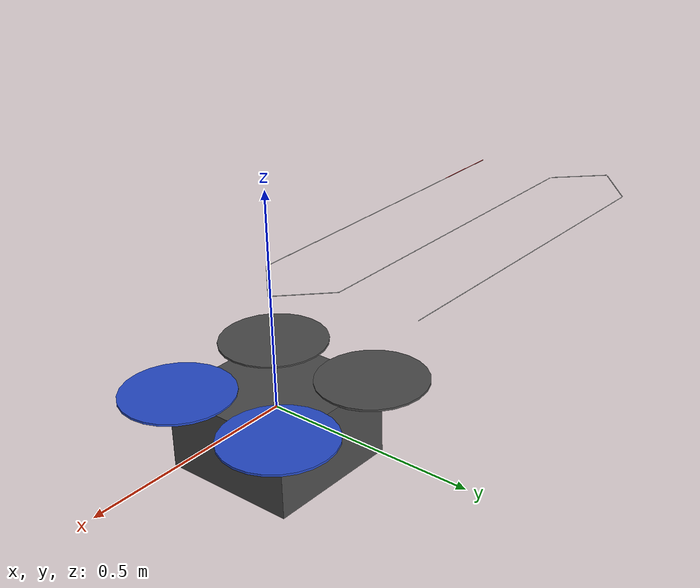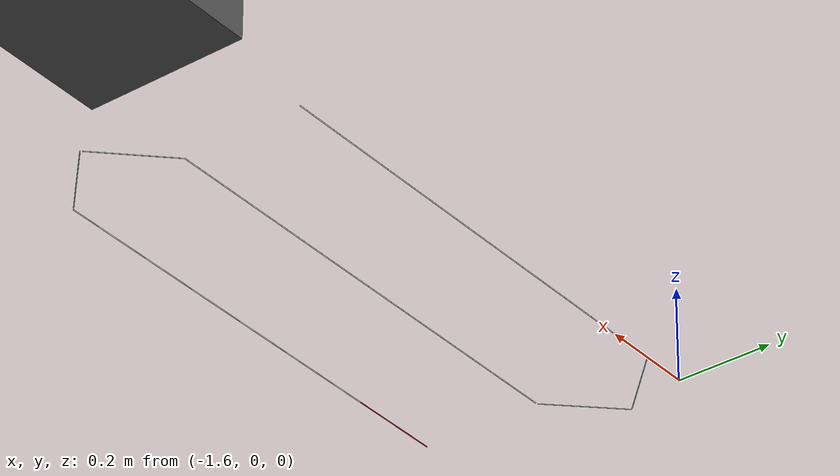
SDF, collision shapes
<sdf version='1.5'>
  <model name='solo_with_tether'>
    <include>
      <uri>model://solo</uri>
    </include>
    <include>
      <uri>model://tether</uri>
      <pose>-0.40 0 0 0 3.1415 0</pose>
    </include>
    <link name='solo_left'>
      <pose>-0.12 0.05 0 0 0 0</pose>
      <inertial>
        <pose>0 0 0 0 0 0</pose>
        <mass>0.005</mass>
        <inertia>
          <ixx>1e-05</ixx>
          <ixy>0</ixy>
          <ixz>0</ixz>
          <iyy>1e-05</iyy>
          <iyz>0</iyz>
          <izz>1e-05</izz>
        </inertia>
      </inertial>
    </link>
    <joint name='solo_left_joint' type='fixed'>
      <child>solo_left</child>
      <parent>solo::base_link</parent>
    </joint>
    <link name='solo_right'>
      <pose>-0.12 -0.05 0 0 0 0</pose>
      <inertial>
        <pose>0 0 0 0 0 0</pose>
        <mass>0.005</mass>
        <inertia>
          <ixx>1e-05</ixx>
          <ixy>0</ixy>
          <ixz>0</ixz>
          <iyy>1e-05</iyy>
          <iyz>0</iyz>
          <izz>1e-05</izz>
        </inertia>
      </inertial>
    </link>
    <joint name='solo_right_joint' type='fixed'>
      <child>solo_right</child>
      <parent>solo::base_link</parent>
    </joint>
    <joint name="tether_solo_right_joint" type="revolute">
      <child>solo_right</child>
      <parent>tether::link_y_left</parent>
      <axis>
	<xyz>0 1 0</xyz>
	<dynamics>
          <damping>0.1</damping>
          <friction>0.0</friction>
          <spring_stiffness>0.05</spring_stiffness>
          <spring_reference>0.0</spring_reference>
        </dynamics>
	<use_parent_model_frame>true</use_parent_model_frame>
      </axis>
      <axis2>
	<xyz>0 0 1</xyz>
	<dynamics>
          <damping>0.1</damping>
          <friction>0.0</friction>
          <spring_stiffness>0.05</spring_stiffness>
          <spring_reference>0.0</spring_reference>
        </dynamics>
	<use_parent_model_frame>true</use_parent_model_frame>
      </axis2>
      <physics>
	<ode>
	  <cfm_damping>1</cfm_damping>
	</ode>
      </physics>
      <sensor name="tether_force_torque" type="force_torque">
	<always_on>true</always_on>
	<update_rate>100</update_rate>
	<force_torque>
	  <frame>child</frame>
	  <measure_direction>child_to_parent</measure_direction>
	</force_torque>
      </sensor>
    </joint>
    <joint name="tether_solo_left_joint" type="revolute">
      <child>solo_left</child>
      <parent>tether::link_y_right</parent>
      <axis>
	<xyz>0 1 0</xyz>
	<dynamics>
          <damping>0.1</damping>
          <friction>0.0</friction>
          <spring_stiffness>0.05</spring_stiffness>
          <spring_reference>0.0</spring_reference>
        </dynamics>
	<use_parent_model_frame>true</use_parent_model_frame>
      </axis>
      <axis2>
	<xyz>0 0 1</xyz>
	<dynamics>
          <damping>0.1</damping>
          <friction>0.0</friction>
          <spring_stiffness>0.05</spring_stiffness>
          <spring_reference>0.0</spring_reference>
        </dynamics>
	<use_parent_model_frame>true</use_parent_model_frame>
      </axis2>
      <physics>
	<ode>
	  <cfm_damping>1</cfm_damping>
	</ode>
      </physics>
      <sensor name="tether_force_torque" type="force_torque">
	<always_on>true</always_on>
	<update_rate>100</update_rate>
	<force_torque>
	  <frame>child</frame>
	  <measure_direction>child_to_parent</measure_direction>
	</force_torque>
      </sensor>
    </joint>
  </model>
</sdf>

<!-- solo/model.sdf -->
<sdf version='1.5'>
  <model name='solo'>
     <plugin name="config" filename="libAircraftConfigPlugin.so">
        <motorCount>4</motorCount>
        <!-- Where is the center of thrust in relation to this specified link -->
        <centerOfThrust>
            <link>imu_link</link>
            <offset>0 0 0.058</offset>
        </centerOfThrust>
        <sensors>
          <sensor type="imu"/>
          <sensor type="esc"/>
      </sensors>
    </plugin>
    <!-- Solo body -->
    <link name='base_link'>
      <pose>0 0 0 0 0 0</pose>
      <inertial>
        <pose>0 0 0 0 0 0</pose>
        <mass>1.47</mass>
        <inertia>
          <ixx>0.011</ixx>
          <ixy>0</ixy>
          <ixz>0</ixz>
          <iyy>0.015</iyy>
          <iyz>0</iyz>
          <izz>0.021</izz>
        </inertia>
      </inertial>
      <collision name='base_link_inertia_collision'>
        <pose>0 0 -0.04 0 0 0</pose>
        <geometry>
          <box>
            <size>0.32 0.32 0.18</size>
          </box>
        </geometry>
        <surface>
          <contact>
            <ode>
              <min_depth>0.001</min_depth>
              <max_vel>0</max_vel>
            </ode>
          </contact>
          <friction>
            <ode/>
          </friction>
        </surface>
      </collision>
      <visual name='base_link_inertia_visual'>
        <pose>0 0 0 0 0 0</pose>
        <geometry>
          <mesh>
            <scale>1 1 1</scale>
            <uri>model://solo/meshes/solo.dae</uri>
          </mesh>
        </geometry>
        <material>
          <script>
            <name>Gazebo/DarkGrey</name>
            <uri>file://media/materials/scripts/gazebo.material</uri>
          </script>
        </material>
      </visual>
      <gravity>1</gravity>
      <velocity_decay/>
      <self_collide>0</self_collide>
    </link>
    <link name='imu_link'>
      <pose>0 0 0 0 0 0</pose>
      <inertial>
        <pose>0 0 0 0 0 0</pose>
        <mass>0.015</mass>
        <inertia>
          <ixx>1e-05</ixx>
          <ixy>0</ixy>
          <ixz>0</ixz>
          <iyy>1e-05</iyy>
          <iyz>0</iyz>
          <izz>1e-05</izz>
        </inertia>
      </inertial>
    </link>
    <joint name='imu_joint' type='revolute'>
      <child>imu_link</child>
      <parent>base_link</parent>
      <axis>
        <xyz>1 0 0</xyz>
        <limit>
          <lower>0</lower>
          <upper>0</upper>
          <effort>0</effort>
          <velocity>0</velocity>
        </limit>
        <dynamics>
          <spring_reference>0</spring_reference>
          <spring_stiffness>0</spring_stiffness>
        </dynamics>
        <use_parent_model_frame>1</use_parent_model_frame>
      </axis>
    </joint>
    <link name='rotor_0'>
      <pose>0.14745 -0.14525 0.051 0 0 0</pose>
      <inertial>
        <pose>0 0 0 0 0 0</pose>
        <mass>0.005</mass>
        <inertia>
          <ixx>9.75e-07</ixx>
          <ixy>0</ixy>
          <ixz>0</ixz>
          <iyy>0.000273104</iyy>
          <iyz>0</iyz>
          <izz>0.000274004</izz>
        </inertia>
      </inertial>
      <collision name='rotor_0_collision'>
        <pose>0 0 0 0 0 0</pose>
        <geometry>
          <cylinder>
            <length>0.005</length>
            <radius>0.128</radius>
          </cylinder>
        </geometry>
        <surface>
          <contact>
            <ode/>
          </contact>
          <friction>
            <ode/>
          </friction>
        </surface>
      </collision>
      <visual name='rotor_0_visual'>
        <pose>-0.14745 -0.14525 -0.051 0 0 0</pose>
        <geometry>
          <mesh>
            <scale>1 1 1</scale>
            <uri>model://solo/meshes/solo_prop_ccw.dae</uri>
          </mesh>
        </geometry>
        <material>
          <script>
            <name>Gazebo/Blue</name>
            <uri>file://media/materials/scripts/gazebo.material</uri>
          </script>
        </material>
      </visual>
      <gravity>1</gravity>
      <velocity_decay/>
      <self_collide>0</self_collide>
    </link>
    <joint name='rotor_0_joint' type='revolute'>
      <child>rotor_0</child>
      <parent>base_link</parent>
      <axis>
        <xyz>0 0 1</xyz>
        <limit>
          <lower>-1e+16</lower>
          <upper>1e+16</upper>
        </limit>
        <dynamics>
          <spring_reference>0</spring_reference>
          <spring_stiffness>0</spring_stiffness>
        </dynamics>
        <use_parent_model_frame>1</use_parent_model_frame>
      </axis>
    </joint>
    <link name='rotor_1'>
      <pose>-0.14745 0.14525 0.051 0 0 0</pose>
      <inertial>
        <pose>0 0 0 0 0 0</pose>
        <mass>0.005</mass>
        <inertia>
          <ixx>9.75e-07</ixx>
          <ixy>0</ixy>
          <ixz>0</ixz>
          <iyy>0.000273104</iyy>
          <iyz>0</iyz>
          <izz>0.000274004</izz>
        </inertia>
      </inertial>
      <collision name='rotor_1_collision'>
        <pose>0 0 0 0 0 0</pose>
        <geometry>
          <cylinder>
            <length>0.005</length>
            <radius>0.128</radius>
          </cylinder>
        </geometry>
        <surface>
          <contact>
            <ode/>
          </contact>
          <friction>
            <ode/>
          </friction>
        </surface>
      </collision>
      <visual name='rotor_1_visual'>
        <pose>-0.14745 -0.14525 -0.051 0 0 0</pose>
        <geometry>
          <mesh>
            <scale>1 1 1</scale>
            <uri>model://solo/meshes/solo_prop_ccw.dae</uri>
          </mesh>
        </geometry>
        <material>
          <script>
            <name>Gazebo/DarkGrey</name>
            <uri>file://media/materials/scripts/gazebo.material</uri>
          </script>
        </material>
      </visual>
      <gravity>1</gravity>
      <velocity_decay/>
      <self_collide>0</self_collide>
    </link>
    <joint name='rotor_1_joint' type='revolute'>
      <child>rotor_1</child>
      <parent>base_link</parent>
      <axis>
        <xyz>0 0 1</xyz>
        <limit>
          <lower>-1e+16</lower>
          <upper>1e+16</upper>
        </limit>
        <dynamics>
          <spring_reference>0</spring_reference>
          <spring_stiffness>0</spring_stiffness>
        </dynamics>
        <use_parent_model_frame>1</use_parent_model_frame>
      </axis>
    </joint>
    <link name='rotor_2'>
      <pose>0.14745 0.14525 0.051 0 0 0</pose>
      <inertial>
        <pose>0 0 0 0 0 0</pose>
        <mass>0.005</mass>
        <inertia>
          <ixx>9.75e-07</ixx>
          <ixy>0</ixy>
          <ixz>0</ixz>
          <iyy>0.000273104</iyy>
          <iyz>0</iyz>
          <izz>0.000274004</izz>
        </inertia>
      </inertial>
      <collision name='rotor_2_collision'>
        <pose>0 0 0 0 0 0</pose>
        <geometry>
          <cylinder>
            <length>0.005</length>
            <radius>0.128</radius>
          </cylinder>
        </geometry>
        <surface>
          <contact>
            <ode/>
          </contact>
          <friction>
            <ode/>
          </friction>
        </surface>
      </collision>
      <visual name='rotor_2_visual'>
        <pose>-0.14745 0.14525 -0.051 0 0 0</pose>
        <geometry>
          <mesh>
            <scale>1 1 1</scale>
            <uri>model://solo/meshes/solo_prop_cw.dae</uri>
          </mesh>
        </geometry>
        <material>
          <script>
            <name>Gazebo/Blue</name>
            <uri>file://media/materials/scripts/gazebo.material</uri>
          </script>
        </material>
      </visual>
      <gravity>1</gravity>
      <velocity_decay/>
      <self_collide>0</self_collide>
    </link>
    <joint name='rotor_2_joint' type='revolute'>
      <child>rotor_2</child>
      <parent>base_link</parent>
      <axis>
        <xyz>0 0 1</xyz>
        <limit>
          <lower>-1e+16</lower>
          <upper>1e+16</upper>
        </limit>
        <dynamics>
          <spring_reference>0</spring_reference>
          <spring_stiffness>0</spring_stiffness>
        </dynamics>
        <use_parent_model_frame>1</use_parent_model_frame>
      </axis>
    </joint>
    <link name='rotor_3'>
      <pose>-0.14745 -0.14525 0.051 0 0 0</pose>
      <inertial>
        <pose>0 0 0 0 0 0</pose>
        <mass>0.005</mass>
        <inertia>
          <ixx>9.75e-07</ixx>
          <ixy>0</ixy>
          <ixz>0</ixz>
          <iyy>0.000273104</iyy>
          <iyz>0</iyz>
          <izz>0.000274004</izz>
        </inertia>
      </inertial>
      <collision name='rotor_3_collision'>
        <pose>0 0 0 0 0 0</pose>
        <geometry>
          <cylinder>
            <length>0.005</length>
            <radius>0.128</radius>
          </cylinder>
        </geometry>
        <surface>
          <contact>
            <ode/>
          </contact>
          <friction>
            <ode/>
          </friction>
        </surface>
      </collision>
      <visual name='rotor_3_visual'>
        <pose>-0.14745 0.14525 -0.051 0 0 0</pose>
        <geometry>
          <mesh>
            <scale>1 1 1</scale>
            <uri>model://solo/meshes/solo_prop_cw.dae</uri>
          </mesh>
        </geometry>
        <material>
          <script>
            <name>Gazebo/DarkGrey</name>
            <uri>file://media/materials/scripts/gazebo.material</uri>
          </script>
        </material>
      </visual>
      <gravity>1</gravity>
      <velocity_decay/>
      <self_collide>0</self_collide>
    </link>
    <joint name='rotor_3_joint' type='revolute'>
      <child>rotor_3</child>
      <parent>base_link</parent>
      <axis>
        <xyz>0 0 1</xyz>
        <limit>
          <lower>-1e+16</lower>
          <upper>1e+16</upper>
        </limit>
        <dynamics>
          <spring_reference>0</spring_reference>
          <spring_stiffness>0</spring_stiffness>
        </dynamics>
        <use_parent_model_frame>1</use_parent_model_frame>
      </axis>
    </joint>
    <plugin name='front_right_motor_model' filename='libgymfc_gazebo_motor_model.so'>
      <robotNamespace></robotNamespace>
      <jointName>rotor_0_joint</jointName>
      <linkName>rotor_0</linkName>
      <turningDirection>ccw</turningDirection>
      <timeConstantUp>0.0125</timeConstantUp>
      <timeConstantDown>0.025</timeConstantDown>
      <maxRotVelocity>1500</maxRotVelocity>
      <motorConstant>8.54858e-06</motorConstant>
      <momentConstant>0.06</momentConstant>
      <motorNumber>0</motorNumber>
      <commandSubTopic>/gazebo/command/motor_speed</commandSubTopic>
      <rotorDragCoefficient>0.000806428</rotorDragCoefficient>
      <rollingMomentCoefficient>1e-06</rollingMomentCoefficient>
      <motorSpeedPubTopic>/motor_speed/0</motorSpeedPubTopic>
      <rotorVelocitySlowdownSim>10</rotorVelocitySlowdownSim>
    </plugin>
    <plugin name='back_left_motor_model' filename='libgymfc_gazebo_motor_model.so'>
      <robotNamespace></robotNamespace>
      <jointName>rotor_1_joint</jointName>
      <linkName>rotor_1</linkName>
      <turningDirection>ccw</turningDirection>
      <timeConstantUp>0.0125</timeConstantUp>
      <timeConstantDown>0.025</timeConstantDown>
      <maxRotVelocity>1500</maxRotVelocity>
      <motorConstant>8.54858e-06</motorConstant>
      <momentConstant>0.06</momentConstant>
      <motorNumber>1</motorNumber>
      <commandSubTopic>/gazebo/command/motor_speed</commandSubTopic>
      <rotorDragCoefficient>0.000806428</rotorDragCoefficient>
      <rollingMomentCoefficient>1e-06</rollingMomentCoefficient>
      <motorSpeedPubTopic>/motor_speed/1</motorSpeedPubTopic>
      <rotorVelocitySlowdownSim>10</rotorVelocitySlowdownSim>
    </plugin>
    <plugin name='front_left_motor_model' filename='libgymfc_gazebo_motor_model.so'>
      <robotNamespace></robotNamespace>
      <jointName>rotor_2_joint</jointName>
      <linkName>rotor_2</linkName>
      <turningDirection>cw</turningDirection>
      <timeConstantUp>0.0125</timeConstantUp>
      <timeConstantDown>0.025</timeConstantDown>
      <maxRotVelocity>1500</maxRotVelocity>
      <motorConstant>8.54858e-06</motorConstant>
      <momentConstant>0.06</momentConstant>
      <motorNumber>2</motorNumber>
      <commandSubTopic>/gazebo/command/motor_speed</commandSubTopic>
      <rotorDragCoefficient>0.000806428</rotorDragCoefficient>
      <rollingMomentCoefficient>1e-06</rollingMomentCoefficient>
      <motorSpeedPubTopic>/motor_speed/2</motorSpeedPubTopic>
      <rotorVelocitySlowdownSim>10</rotorVelocitySlowdownSim>
    </plugin>
    <plugin name='back_right_motor_model' filename='libgymfc_gazebo_motor_model.so'>
      <robotNamespace></robotNamespace>
      <jointName>rotor_3_joint</jointName>
      <linkName>rotor_3</linkName>
      <turningDirection>cw</turningDirection>
      <timeConstantUp>0.0125</timeConstantUp>
      <timeConstantDown>0.025</timeConstantDown>
      <maxRotVelocity>1500</maxRotVelocity>
      <motorConstant>8.54858e-06</motorConstant>
      <momentConstant>0.06</momentConstant>
      <motorNumber>3</motorNumber>
      <commandSubTopic>/gazebo/command/motor_speed</commandSubTopic>
      <rotorDragCoefficient>0.000806428</rotorDragCoefficient>
      <rollingMomentCoefficient>1e-06</rollingMomentCoefficient>
      <motorSpeedPubTopic>/motor_speed/3</motorSpeedPubTopic>
      <rotorVelocitySlowdownSim>10</rotorVelocitySlowdownSim>
    </plugin>
    <plugin name='rotors_gazebo_imu_plugin' filename='libgymfc_gazebo_imu_plugin.so'>
      <robotNamespace></robotNamespace>
      <linkName>imu_link</linkName>
      <imuTopic>/imu</imuTopic>
      <gyroscopeNoiseDensity>0.0003394</gyroscopeNoiseDensity>
      <gyroscopeRandomWalk>3.8785e-05</gyroscopeRandomWalk>
      <gyroscopeBiasCorrelationTime>1000.0</gyroscopeBiasCorrelationTime>
      <gyroscopeTurnOnBiasSigma>0.0087</gyroscopeTurnOnBiasSigma>
      <accelerometerNoiseDensity>0.004</accelerometerNoiseDensity>
      <accelerometerRandomWalk>0.006</accelerometerRandomWalk>
      <accelerometerBiasCorrelationTime>300.0</accelerometerBiasCorrelationTime>
      <accelerometerTurnOnBiasSigma>0.196</accelerometerTurnOnBiasSigma>
    </plugin>
    <static>0</static>
  </model>
</sdf>

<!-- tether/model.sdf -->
<sdf version="1.5">
  <model name="tether">
    <pose>-1.81 -4.23 0.055 0 0 0</pose>
    <link name="link_00">
      <gravity>true</gravity>
      <pose>0.1 0 0 0 0 0</pose>
      <inertial>
        <mass>0.009</mass>
        <pose>0.1 0 0 0 0 0</pose>
        <inertia>
          <ixx>0.01</ixx>
          <ixy>0</ixy>
          <ixz>0</ixz>
          <iyy>0.01</iyy>
          <iyz>0</iyz>
          <izz>0.01</izz>
        </inertia>
      </inertial>
      <visual name="sphere">
        <geometry>
          <sphere>
            <radius>0.009</radius>
          </sphere>
        </geometry>
        <material>
	  <script>
            <name>Gazebo/Red</name>
            <uri>file://media/materials/scripts/gazebo.material</uri>
          </script>
        </material>
      </visual>
    </link>
    <link name="link_01">
      <gravity>true</gravity>
      <pose>0.1 0 0 0 0 0</pose>
      <inertial>
        <mass>0.009</mass>
        <pose>0.1 0 0 0 0 0</pose>
        <inertia>
          <ixx>0.01</ixx>
          <ixy>0</ixy>
          <ixz>0</ixz>
          <iyy>0.01</iyy>
          <iyz>0</iyz>
          <izz>0.01</izz>
        </inertia>
      </inertial>
      <collision name="collision">
        <pose>0.1 0 0 0 1.570790 0</pose>
        <geometry>
          <cylinder>
            <length>0.2</length>
            <radius>0.001</radius>
          </cylinder>
        </geometry>
        <surface>
          <contact>
            <ode>
              <min_depth>0.00005</min_depth>
            </ode>
          </contact>
          <friction>
            <ode>
              <mu>1.0</mu>
              <mu2>1.0</mu2>
            </ode>
          </friction>
        </surface>
      </collision>
      <visual name="visual">
        <pose>0.1 0 0 0 1.570790 0</pose>
        <geometry>
          <cylinder>
            <length>0.2</length>
            <radius>0.001</radius>
          </cylinder>
        </geometry>
	<material>
	  <script>
            <name>Gazebo/White</name>
            <uri>file://media/materials/scripts/gazebo.material</uri>
          </script>
        </material>
      </visual>
    </link>
    <link name="link_02">
      <gravity>true</gravity>
      <pose>0.3 0 0 0 0 0</pose>
      <inertial>
        <mass>0.009</mass>
        <pose>0.1 0 0 0 0 0</pose>
        <inertia>
          <ixx>0.01</ixx>
          <ixy>0</ixy>
          <ixz>0</ixz>
          <iyy>0.01</iyy>
          <iyz>0</iyz>
          <izz>0.01</izz>
        </inertia>
      </inertial>
      <collision name="collision">
        <pose>0.1 0 0 0 1.570790 0</pose>
        <geometry>
          <cylinder>
            <length>0.2</length>
            <radius>0.001</radius>
          </cylinder>
        </geometry>
        <surface>
          <contact>
            <ode>
              <min_depth>0.00005</min_depth>
            </ode>
          </contact>
          <friction>
            <ode>
              <mu>1.0</mu>
              <mu2>1.0</mu2>
            </ode>
          </friction>
        </surface>
      </collision>
      <visual name="visual">
        <pose>0.1 0 0 0 1.570790 0</pose>
        <geometry>
          <cylinder>
            <length>0.2</length>
            <radius>0.001</radius>
          </cylinder>
        </geometry>
	<material>
	  <script>
            <name>Gazebo/White</name>
            <uri>file://media/materials/scripts/gazebo.material</uri>
          </script>
        </material>
      </visual>
      <visual name="sphere">
        <geometry>
          <sphere>
            <radius>0.009</radius>
          </sphere>
        </geometry>
        <material>
	  <script>
            <name>Gazebo/Red</name>
            <uri>file://media/materials/scripts/gazebo.material</uri>
          </script>
        </material>
      </visual>
    </link>
    <link name="link_03">
      <gravity>true</gravity>
      <pose>0.5 0 0 0 0 0</pose>
      <inertial>
        <mass>0.009</mass>
        <pose>0.1 0 0 0 0 0</pose>
        <inertia>
          <ixx>0.01</ixx>
          <ixy>0</ixy>
          <ixz>0</ixz>
          <iyy>0.01</iyy>
          <iyz>0</iyz>
          <izz>0.01</izz>
        </inertia>
      </inertial>
      <collision name="collision">
        <pose>0.1 0 0 0 1.570790 0</pose>
        <geometry>
          <cylinder>
            <length>0.2</length>
            <radius>0.001</radius>
          </cylinder>
        </geometry>
        <surface>
          <contact>
            <ode>
              <min_depth>0.00005</min_depth>
            </ode>
          </contact>
          <friction>
            <ode>
              <mu>1.0</mu>
              <mu2>1.0</mu2>
            </ode>
          </friction>
        </surface>
      </collision>
      <visual name="visual">
        <pose>0.1 0 0 0 1.570790 0</pose>
        <geometry>
          <cylinder>
            <length>0.2</length>
            <radius>0.001</radius>
          </cylinder>
        </geometry>
	<material>
	  <script>
            <name>Gazebo/White</name>
            <uri>file://media/materials/scripts/gazebo.material</uri>
          </script>
        </material>
      </visual>
      <visual name="sphere">
        <geometry>
          <sphere>
            <radius>0.009</radius>
          </sphere>
        </geometry>
        <material>
	  <script>
            <name>Gazebo/Red</name>
            <uri>file://media/materials/scripts/gazebo.material</uri>
          </script>
        </material>
      </visual>
    </link>
    <link name="link_04">
      <gravity>true</gravity>
      <pose>0.7 0 0 0 0 0</pose>
      <inertial>
        <mass>0.009</mass>
        <pose>0.1 0 0 0 0 0</pose>
        <inertia>
          <ixx>0.01</ixx>
          <ixy>0</ixy>
          <ixz>0</ixz>
          <iyy>0.01</iyy>
          <iyz>0</iyz>
          <izz>0.01</izz>
        </inertia>
      </inertial>
      <collision name="collision">
        <pose>0.1 0 0 0 1.570790 0</pose>
        <geometry>
          <cylinder>
            <length>0.2</length>
            <radius>0.001</radius>
          </cylinder>
        </geometry>
        <surface>
          <contact>
            <ode>
              <min_depth>0.00005</min_depth>
            </ode>
          </contact>
          <friction>
            <ode>
              <mu>1.0</mu>
              <mu2>1.0</mu2>
            </ode>
          </friction>
        </surface>
      </collision>
      <visual name="visual">
        <pose>0.1 0 0 0 1.570790 0</pose>
        <geometry>
          <cylinder>
            <length>0.2</length>
            <radius>0.001</radius>
          </cylinder>
        </geometry>
	<material>
	  <script>
            <name>Gazebo/White</name>
            <uri>file://media/materials/scripts/gazebo.material</uri>
          </script>
        </material>
      </visual>
      <visual name="sphere">
        <geometry>
          <sphere>
            <radius>0.009</radius>
          </sphere>
        </geometry>
        <material>
	  <script>
            <name>Gazebo/Red</name>
            <uri>file://media/materials/scripts/gazebo.material</uri>
          </script>
        </material>
      </visual>
    </link>
    <link name="link_05">
      <gravity>true</gravity>
      <pose>0.9 0 0 0 0 0</pose>
      <inertial>
        <mass>0.009</mass>
        <pose>0.1 0 0 0 0 0</pose>
        <inertia>
          <ixx>0.01</ixx>
          <ixy>0</ixy>
          <ixz>0</ixz>
          <iyy>0.01</iyy>
          <iyz>0</iyz>
          <izz>0.01</izz>
        </inertia>
      </inertial>
      <collision name="collision">
        <pose>0.1 0 0 0 1.570790 0</pose>
        <geometry>
          <cylinder>
            <length>0.2</length>
            <radius>0.001</radius>
          </cylinder>
        </geometry>
        <surface>
          <contact>
            <ode>
              <min_depth>0.00005</min_depth>
            </ode>
          </contact>
          <friction>
            <ode>
              <mu>1.0</mu>
              <mu2>1.0</mu2>
            </ode>
          </friction>
        </surface>
      </collision>
      <visual name="visual">
        <pose>0.1 0 0 0 1.570790 0</pose>
        <geometry>
          <cylinder>
            <length>0.2</length>
            <radius>0.001</radius>
          </cylinder>
        </geometry>
	<material>
	  <script>
            <name>Gazebo/White</name>
            <uri>file://media/materials/scripts/gazebo.material</uri>
          </script>
        </material>
      </visual>
      <visual name="sphere">
        <geometry>
          <sphere>
            <radius>0.009</radius>
          </sphere>
        </geometry>
        <material>
	  <script>
            <name>Gazebo/Red</name>
            <uri>file://media/materials/scripts/gazebo.material</uri>
          </script>
        </material>
      </visual>
    </link>
    <link name="link_06">
      <gravity>true</gravity>
      <pose>1.1 0 0 0 0 -.785</pose>
      <inertial>
        <mass>0.009</mass>
        <pose>0.0875 0 0 0 0 0</pose>
        <inertia>
          <ixx>0.01</ixx>
          <ixy>0</ixy>
          <ixz>0</ixz>
          <iyy>0.01</iyy>
          <iyz>0</iyz>
          <izz>0.01</izz>
        </inertia>
      </inertial>
      <collision name="collision">
        <pose>0.0875 0 0 0 1.570790 0</pose>
        <geometry>
          <cylinder>
            <length>0.175</length>
            <radius>0.001</radius>
          </cylinder>
        </geometry>
        <surface>
          <contact>
            <ode>
              <min_depth>0.00005</min_depth>
            </ode>
          </contact>
          <friction>
            <ode>
              <mu>1.0</mu>
              <mu2>1.0</mu2>
            </ode>
          </friction>
        </surface>
      </collision>
      <visual name="visual">
        <pose>0.0875 0 0 0 1.570790 0</pose>
        <geometry>
          <cylinder>
            <length>0.175</length>
            <radius>0.001</radius>
          </cylinder>
        </geometry>
	<material>
	  <script>
            <name>Gazebo/White</name>
            <uri>file://media/materials/scripts/gazebo.material</uri>
          </script>
        </material>
      </visual>
      <visual name="sphere">
        <geometry>
          <sphere>
            <radius>0.009</radius>
          </sphere>
        </geometry>
        <material>
	  <script>
            <name>Gazebo/Red</name>
            <uri>file://media/materials/scripts/gazebo.material</uri>
          </script>
        </material>
      </visual>
    </link>
    <link name="link_07">
      <gravity>true</gravity>
      <pose>1.227 -.127 0 0 0 -2.3415</pose>
      <inertial>
        <mass>0.009</mass>
        <pose>0.0875 0 0 0 0 0</pose>
        <inertia>
          <ixx>0.01</ixx>
          <ixy>0</ixy>
          <ixz>0</ixz>
          <iyy>0.01</iyy>
          <iyz>0</iyz>
          <izz>0.01</izz>
        </inertia>
      </inertial>
      <collision name="collision">
        <pose>0.0875 0 0 0 1.570790 0</pose>
        <geometry>
          <cylinder>
            <length>0.175</length>
            <radius>0.001</radius>
          </cylinder>
        </geometry>
        <surface>
          <contact>
            <ode>
              <min_depth>0.00005</min_depth>
            </ode>
          </contact>
          <friction>
            <ode>
              <mu>1.0</mu>
              <mu2>1.0</mu2>
            </ode>
          </friction>
        </surface>
      </collision>
      <visual name="visual">
        <pose>0.0875 0 0 0 1.570790 0</pose>
        <geometry>
          <cylinder>
            <length>0.175</length>
            <radius>0.001</radius>
          </cylinder>
        </geometry>
	<material>
	  <script>
            <name>Gazebo/White</name>
            <uri>file://media/materials/scripts/gazebo.material</uri>
          </script>
        </material>
      </visual>
      <visual name="sphere">
        <geometry>
          <sphere>
            <radius>0.009</radius>
          </sphere>
        </geometry>
        <material>
	  <script>
            <name>Gazebo/Red</name>
            <uri>file://media/materials/scripts/gazebo.material</uri>
          </script>
        </material>
      </visual>
    </link>
    <link name="link_08">
      <gravity>true</gravity>
      <pose>1.1 -.254 0 0 0 -3.1415</pose>
      <inertial>
        <mass>0.009</mass>
        <pose>0.1 0 0 0 0 0</pose>
        <inertia>
          <ixx>0.01</ixx>
          <ixy>0</ixy>
          <ixz>0</ixz>
          <iyy>0.01</iyy>
          <iyz>0</iyz>
          <izz>0.01</izz>
        </inertia>
      </inertial>
      <collision name="collision">
        <pose>0.1 0 0 0 1.570790 0</pose>
        <geometry>
          <cylinder>
            <length>0.2</length>
            <radius>0.001</radius>
          </cylinder>
        </geometry>
        <surface>
          <contact>
            <ode>
              <min_depth>0.00005</min_depth>
            </ode>
          </contact>
          <friction>
            <ode>
              <mu>1.0</mu>
              <mu2>1.0</mu2>
            </ode>
          </friction>
        </surface>
      </collision>
      <visual name="visual">
        <pose>0.1 0 0 0 1.570790 0</pose>
        <geometry>
          <cylinder>
            <length>0.2</length>
            <radius>0.001</radius>
          </cylinder>
        </geometry>
	<material>
	  <script>
            <name>Gazebo/White</name>
            <uri>file://media/materials/scripts/gazebo.material</uri>
          </script>
        </material>
      </visual>
      <visual name="sphere">
        <geometry>
          <sphere>
            <radius>0.009</radius>
          </sphere>
        </geometry>
        <material>
	  <script>
            <name>Gazebo/Red</name>
            <uri>file://media/materials/scripts/gazebo.material</uri>
          </script>
        </material>
      </visual>
    </link>
    <link name="link_09">
      <gravity>true</gravity>
      <pose>0.9 -.254 0 0 0 -3.1415</pose>
      <inertial>
        <mass>0.009</mass>
        <pose>0.1 0 0 0 0 0</pose>
        <inertia>
          <ixx>0.01</ixx>
          <ixy>0</ixy>
          <ixz>0</ixz>
          <iyy>0.01</iyy>
          <iyz>0</iyz>
          <izz>0.01</izz>
        </inertia>
      </inertial>
      <collision name="collision">
        <pose>0.1 0 0 0 1.570790 0</pose>
        <geometry>
          <cylinder>
            <length>0.2</length>
            <radius>0.001</radius>
          </cylinder>
        </geometry>
        <surface>
          <contact>
            <ode>
              <min_depth>0.00005</min_depth>
            </ode>
          </contact>
          <friction>
            <ode>
              <mu>1.0</mu>
              <mu2>1.0</mu2>
            </ode>
          </friction>
        </surface>
      </collision>
      <visual name="visual">
        <pose>0.1 0 0 0 1.570790 0</pose>
        <geometry>
          <cylinder>
            <length>0.2</length>
            <radius>0.001</radius>
          </cylinder>
        </geometry>
	<material>
	  <script>
            <name>Gazebo/White</name>
            <uri>file://media/materials/scripts/gazebo.material</uri>
          </script>
        </material>
      </visual>
      <visual name="sphere">
        <geometry>
          <sphere>
            <radius>0.009</radius>
          </sphere>
        </geometry>
        <material>
	  <script>
            <name>Gazebo/Red</name>
            <uri>file://media/materials/scripts/gazebo.material</uri>
          </script>
        </material>
      </visual>
    </link>
    <link name="link_10">
      <gravity>true</gravity>
      <pose>0.7 -.254 0 0 0 -3.1415</pose>
      <inertial>
        <mass>0.009</mass>
        <pose>0.1 0 0 0 0 0</pose>
        <inertia>
          <ixx>0.01</ixx>
          <ixy>0</ixy>
          <ixz>0</ixz>
          <iyy>0.01</iyy>
          <iyz>0</iyz>
          <izz>0.01</izz>
        </inertia>
      </inertial>
      <collision name="collision">
        <pose>0.1 0 0 0 1.570790 0</pose>
        <geometry>
          <cylinder>
            <length>0.2</length>
            <radius>0.001</radius>
          </cylinder>
        </geometry>
        <surface>
          <contact>
            <ode>
              <min_depth>0.00005</min_depth>
            </ode>
          </contact>
          <friction>
            <ode>
              <mu>1.0</mu>
              <mu2>1.0</mu2>
            </ode>
          </friction>
        </surface>
      </collision>
      <visual name="visual">
        <pose>0.1 0 0 0 1.570790 0</pose>
        <geometry>
          <cylinder>
            <length>0.2</length>
            <radius>0.001</radius>
          </cylinder>
        </geometry>
	<material>
	  <script>
            <name>Gazebo/White</name>
            <uri>file://media/materials/scripts/gazebo.material</uri>
          </script>
        </material>
      </visual>
      <visual name="sphere">
        <geometry>
          <sphere>
            <radius>0.009</radius>
          </sphere>
        </geometry>
        <material>
	  <script>
            <name>Gazebo/Red</name>
            <uri>file://media/materials/scripts/gazebo.material</uri>
          </script>
        </material>
      </visual>
    </link>
    <link name="link_11">
      <gravity>true</gravity>
      <pose>0.5 -.254 0 0 0 -3.1415</pose>
      <inertial>
        <mass>0.009</mass>
        <pose>0.1 0 0 0 0 0</pose>
        <inertia>
          <ixx>0.01</ixx>
          <ixy>0</ixy>
          <ixz>0</ixz>
          <iyy>0.01</iyy>
          <iyz>0</iyz>
          <izz>0.01</izz>
        </inertia>
      </inertial>
      <collision name="collision">
        <pose>0.1 0 0 0 1.570790 0</pose>
        <geometry>
          <cylinder>
            <length>0.2</length>
            <radius>0.001</radius>
          </cylinder>
        </geometry>
        <surface>
          <contact>
            <ode>
              <min_depth>0.00005</min_depth>
            </ode>
          </contact>
          <friction>
            <ode>
              <mu>1.0</mu>
              <mu2>1.0</mu2>
            </ode>
          </friction>
        </surface>
      </collision>
      <visual name="visual">
        <pose>0.1 0 0 0 1.570790 0</pose>
        <geometry>
          <cylinder>
            <length>0.2</length>
            <radius>0.001</radius>
          </cylinder>
        </geometry>
	<material>
	  <script>
            <name>Gazebo/White</name>
            <uri>file://media/materials/scripts/gazebo.material</uri>
          </script>
        </material>
      </visual>
      <visual name="sphere">
        <geometry>
          <sphere>
            <radius>0.009</radius>
          </sphere>
        </geometry>
        <material>
	  <script>
            <name>Gazebo/Red</name>
            <uri>file://media/materials/scripts/gazebo.material</uri>
          </script>
        </material>
      </visual>
    </link>
    <link name="link_12">
      <gravity>true</gravity>
      <pose>0.3 -.254 0 0 0 -3.1415</pose>
      <inertial>
        <mass>0.009</mass>
        <pose>0.1 0 0 0 0 0</pose>
        <inertia>
          <ixx>0.01</ixx>
          <ixy>0</ixy>
          <ixz>0</ixz>
          <iyy>0.01</iyy>
          <iyz>0</iyz>
          <izz>0.01</izz>
        </inertia>
      </inertial>
      <collision name="collision">
        <pose>0.1 0 0 0 1.570790 0</pose>
        <geometry>
          <cylinder>
            <length>0.2</length>
            <radius>0.001</radius>
          </cylinder>
        </geometry>
        <surface>
          <contact>
            <ode>
              <min_depth>0.00005</min_depth>
            </ode>
          </contact>
          <friction>
            <ode>
              <mu>1.0</mu>
              <mu2>1.0</mu2>
            </ode>
          </friction>
        </surface>
      </collision>
      <visual name="visual">
        <pose>0.1 0 0 0 1.570790 0</pose>
        <geometry>
          <cylinder>
            <length>0.2</length>
            <radius>0.001</radius>
          </cylinder>
        </geometry>
	<material>
	  <script>
            <name>Gazebo/White</name>
            <uri>file://media/materials/scripts/gazebo.material</uri>
          </script>
        </material>
      </visual>
      <visual name="sphere">
        <geometry>
          <sphere>
            <radius>0.009</radius>
          </sphere>
        </geometry>
        <material>
	  <script>
            <name>Gazebo/Red</name>
            <uri>file://media/materials/scripts/gazebo.material</uri>
          </script>
        </material>
      </visual>
    </link>
    <link name="link_13">
      <gravity>true</gravity>
      <pose>0.1 -.254 0 0 0 -2.356</pose>
      <inertial>
        <mass>0.009</mass>
        <pose>0.0875 0 0 0 0 0</pose>
        <inertia>
          <ixx>0.01</ixx>
          <ixy>0</ixy>
          <ixz>0</ixz>
          <iyy>0.01</iyy>
          <iyz>0</iyz>
          <izz>0.01</izz>
        </inertia>
      </inertial>
      <collision name="collision">
        <pose>0.0875 0 0 0 1.570790 0</pose>
        <geometry>
          <cylinder>
            <length>0.175</length>
            <radius>0.001</radius>
          </cylinder>
        </geometry>
        <surface>
          <contact>
            <ode>
              <min_depth>0.00005</min_depth>
            </ode>
          </contact>
          <friction>
            <ode>
              <mu>1.0</mu>
              <mu2>1.0</mu2>
            </ode>
          </friction>
        </surface>
      </collision>
      <visual name="visual">
        <pose>0.0875 0 0 0 1.570790 0</pose>
        <geometry>
          <cylinder>
            <length>0.175</length>
            <radius>0.001</radius>
          </cylinder>
        </geometry>
	<material>
	  <script>
            <name>Gazebo/White</name>
            <uri>file://media/materials/scripts/gazebo.material</uri>
          </script>
        </material>
      </visual>
      <visual name="sphere">
        <geometry>
          <sphere>
            <radius>0.009</radius>
          </sphere>
        </geometry>
        <material>
	  <script>
            <name>Gazebo/Red</name>
            <uri>file://media/materials/scripts/gazebo.material</uri>
          </script>
        </material>
      </visual>
    </link>
    <link name="link_14">
      <gravity>true</gravity>
      <pose>-0.027 -.381 0 0 0 -.785</pose>
      <inertial>
        <mass>0.009</mass>
        <pose>0.0875 0 0 0 0 0</pose>
        <inertia>
          <ixx>0.01</ixx>
          <ixy>0</ixy>
          <ixz>0</ixz>
          <iyy>0.01</iyy>
          <iyz>0</iyz>
          <izz>0.01</izz>
        </inertia>
      </inertial>
      <collision name="collision">
        <pose>0.0875 0 0 0 1.570790 0</pose>
        <geometry>
          <cylinder>
            <length>0.175</length>
            <radius>0.001</radius>
          </cylinder>
        </geometry>
        <surface>
          <contact>
            <ode>
              <min_depth>0.00005</min_depth>
            </ode>
          </contact>
          <friction>
            <ode>
              <mu>1.0</mu>
              <mu2>1.0</mu2>
            </ode>
          </friction>
        </surface>
      </collision>
      <visual name="visual">
        <pose>0.0875 0 0 0 1.570790 0</pose>
        <geometry>
          <cylinder>
            <length>0.175</length>
            <radius>0.001</radius>
          </cylinder>
        </geometry>
	<material>
	  <script>
            <name>Gazebo/White</name>
            <uri>file://media/materials/scripts/gazebo.material</uri>
          </script>
        </material>
      </visual>
      <visual name="sphere">
        <geometry>
          <sphere>
            <radius>0.009</radius>
          </sphere>
        </geometry>
        <material>
	  <script>
            <name>Gazebo/Red</name>
            <uri>file://media/materials/scripts/gazebo.material</uri>
          </script>
        </material>
      </visual>
    </link>
    <link name="link_15">
      <gravity>true</gravity>
      <pose>0.1 -.508 0 0 0 0</pose>
      <inertial>
        <mass>0.009</mass>
        <pose>0.1 0 0 0 0 0</pose>
        <inertia>
          <ixx>0.01</ixx>
          <ixy>0</ixy>
          <ixz>0</ixz>
          <iyy>0.01</iyy>
          <iyz>0</iyz>
          <izz>0.01</izz>
        </inertia>
      </inertial>
      <collision name="collision">
        <pose>0.1 0 0 0 1.570790 0</pose>
        <geometry>
          <cylinder>
            <length>0.2</length>
            <radius>0.001</radius>
          </cylinder>
        </geometry>
        <surface>
          <contact>
            <ode>
              <min_depth>0.00005</min_depth>
            </ode>
          </contact>
          <friction>
            <ode>
              <mu>1.0</mu>
              <mu2>1.0</mu2>
            </ode>
          </friction>
        </surface>
      </collision>
      <visual name="visual">
        <pose>0.1 0 0 0 1.570790 0</pose>
        <geometry>
          <cylinder>
            <length>0.2</length>
            <radius>0.001</radius>
          </cylinder>
        </geometry>
	<material>
	  <script>
            <name>Gazebo/White</name>
            <uri>file://media/materials/scripts/gazebo.material</uri>
          </script>
        </material>
      </visual>
      <visual name="sphere">
        <geometry>
          <sphere>
            <radius>0.009</radius>
          </sphere>
        </geometry>
        <material>
	  <script>
            <name>Gazebo/Red</name>
            <uri>file://media/materials/scripts/gazebo.material</uri>
          </script>
        </material>
      </visual>
    </link>
    <link name="link_16">
      <gravity>true</gravity>
      <pose>0.3 -.508 0 0 0 0</pose>
      <inertial>
        <mass>0.009</mass>
        <pose>0.1 0 0 0 0 0</pose>
        <inertia>
          <ixx>0.01</ixx>
          <ixy>0</ixy>
          <ixz>0</ixz>
          <iyy>0.01</iyy>
          <iyz>0</iyz>
          <izz>0.01</izz>
        </inertia>
      </inertial>
      <collision name="collision">
        <pose>0.1 0 0 0 1.570790 0</pose>
        <geometry>
          <cylinder>
            <length>0.2</length>
            <radius>0.001</radius>
          </cylinder>
        </geometry>
        <surface>
          <contact>
            <ode>
              <min_depth>0.00005</min_depth>
            </ode>
          </contact>
          <friction>
            <ode>
              <mu>1.0</mu>
              <mu2>1.0</mu2>
            </ode>
          </friction>
        </surface>
      </collision>
      <visual name="visual">
        <pose>0.1 0 0 0 1.570790 0</pose>
        <geometry>
          <cylinder>
            <length>0.2</length>
            <radius>0.001</radius>
          </cylinder>
        </geometry>
	<material>
	  <script>
            <name>Gazebo/White</name>
            <uri>file://media/materials/scripts/gazebo.material</uri>
          </script>
        </material>
      </visual>
      <visual name="sphere">
        <geometry>
          <sphere>
            <radius>0.009</radius>
          </sphere>
        </geometry>
        <material>
	  <script>
            <name>Gazebo/Red</name>
            <uri>file://media/materials/scripts/gazebo.material</uri>
          </script>
        </material>
      </visual>
    </link>
    <link name="link_17">
      <gravity>true</gravity>
      <pose>0.5 -.508 0 0 0 0</pose>
      <inertial>
        <mass>0.009</mass>
        <pose>0.1 0 0 0 0 0</pose>
        <inertia>
          <ixx>0.01</ixx>
          <ixy>0</ixy>
          <ixz>0</ixz>
          <iyy>0.01</iyy>
          <iyz>0</iyz>
          <izz>0.01</izz>
        </inertia>
      </inertial>
      <collision name="collision">
        <pose>0.1 0 0 0 1.570790 0</pose>
        <geometry>
          <cylinder>
            <length>0.2</length>
            <radius>0.001</radius>
          </cylinder>
        </geometry>
        <surface>
          <contact>
            <ode>
              <min_depth>0.00005</min_depth>
            </ode>
          </contact>
          <friction>
            <ode>
              <mu>1.0</mu>
              <mu2>1.0</mu2>
            </ode>
          </friction>
        </surface>
      </collision>
      <visual name="visual">
        <pose>0.1 0 0 0 1.570790 0</pose>
        <geometry>
          <cylinder>
            <length>0.2</length>
            <radius>0.001</radius>
          </cylinder>
        </geometry>
	<material>
	  <script>
            <name>Gazebo/White</name>
            <uri>file://media/materials/scripts/gazebo.material</uri>
          </script>
        </material>
      </visual>
      <visual name="sphere">
        <geometry>
          <sphere>
            <radius>0.009</radius>
          </sphere>
        </geometry>
        <material>
	  <script>
            <name>Gazebo/Red</name>
            <uri>file://media/materials/scripts/gazebo.material</uri>
          </script>
        </material>
      </visual>
    </link>
    <link name="link_18">
      <gravity>true</gravity>
      <pose>0.7 -.508 0 0 0 0</pose>
      <inertial>
        <mass>0.009</mass>
        <pose>0.1 0 0 0 0 0</pose>
        <inertia>
          <ixx>0.01</ixx>
          <ixy>0</ixy>
          <ixz>0</ixz>
          <iyy>0.01</iyy>
          <iyz>0</iyz>
          <izz>0.01</izz>
        </inertia>
      </inertial>
      <collision name="collision">
        <pose>0.1 0 0 0 1.570790 0</pose>
        <geometry>
          <cylinder>
            <length>0.2</length>
            <radius>0.001</radius>
          </cylinder>
        </geometry>
        <surface>
          <contact>
            <ode>
              <min_depth>0.00005</min_depth>
            </ode>
          </contact>
          <friction>
            <ode>
              <mu>1.0</mu>
              <mu2>1.0</mu2>
            </ode>
          </friction>
        </surface>
      </collision>
      <visual name="visual">
        <pose>0.1 0 0 0 1.570790 0</pose>
        <geometry>
          <cylinder>
            <length>0.2</length>
            <radius>0.001</radius>
          </cylinder>
        </geometry>
	<material>
	  <script>
            <name>Gazebo/White</name>
            <uri>file://media/materials/scripts/gazebo.material</uri>
          </script>
        </material>
      </visual>
      <visual name="sphere">
        <geometry>
          <sphere>
            <radius>0.009</radius>
          </sphere>
        </geometry>
        <material>
	  <script>
            <name>Gazebo/Red</name>
            <uri>file://media/materials/scripts/gazebo.material</uri>
          </script>
        </material>
      </visual>
    </link>
    <link name="link_19">
      <gravity>true</gravity>
      <pose>0.9 -.508 0 0 0 0</pose>
      <inertial>
        <mass>0.009</mass>
        <pose>0.1 0 0 0 0 0</pose>
        <inertia>
          <ixx>0.01</ixx>
          <ixy>0</ixy>
          <ixz>0</ixz>
          <iyy>0.01</iyy>
          <iyz>0</iyz>
          <izz>0.01</izz>
        </inertia>
      </inertial>
      <collision name="collision">
        <pose>0.1 0 0 0 1.570790 0</pose>
        <geometry>
          <cylinder>
            <length>0.2</length>
            <radius>0.001</radius>
          </cylinder>
        </geometry>
        <surface>
          <contact>
            <ode>
              <min_depth>0.00005</min_depth>
            </ode>
          </contact>
          <friction>
            <ode>
              <mu>1.0</mu>
              <mu2>1.0</mu2>
            </ode>
          </friction>
        </surface>
      </collision>
      <visual name="sphere">
        <geometry>
          <sphere>
            <radius>0.009</radius>
          </sphere>
        </geometry>
        <material>
	  <script>
            <name>Gazebo/Red</name>
            <uri>file://media/materials/scripts/gazebo.material</uri>
          </script>
        </material>
      </visual>
    </link>
    <joint name="joint_01" type="universal">
      <child>link_01</child>
      <parent>link_00</parent>
      <axis>
        <xyz>0 1 0</xyz>
        <limit>
          <lower>-1.57</lower>
          <upper>1.57</upper>
        </limit>
        <dynamics>
          <damping>0.1</damping>
          <friction>0.0</friction>
          <spring_stiffness>0.05</spring_stiffness>
          <spring_reference>0.0</spring_reference>
        </dynamics>
        <use_parent_model_frame>true</use_parent_model_frame>
      </axis>
      <axis2>
        <xyz>0 0 1</xyz>
        <limit>
          <lower>-1.57</lower>
          <upper>1.57</upper>
        </limit>
        <dynamics>
          <damping>0.1</damping>
          <friction>0.0</friction>
          <spring_stiffness>0.05</spring_stiffness>
          <spring_reference>0.0</spring_reference>
        </dynamics>
        <use_parent_model_frame>true</use_parent_model_frame>
      </axis2>
      <physics>
        <ode>
          <cfm_damping>1</cfm_damping>
        </ode>
      </physics>
    </joint>
    <joint name="joint_02" type="universal">
      <child>link_02</child>
      <parent>link_01</parent>
      <axis>
        <xyz>0 1 0</xyz>
        <limit>
          <lower>-1.57</lower>
          <upper>1.57</upper>
        </limit>
        <dynamics>
          <damping>0.1</damping>
          <friction>0.0</friction>
          <spring_stiffness>0.05</spring_stiffness>
          <spring_reference>0.0</spring_reference>
        </dynamics>
        <use_parent_model_frame>true</use_parent_model_frame>
      </axis>
      <axis2>
        <xyz>0 0 1</xyz>
        <limit>
          <lower>-1.57</lower>
          <upper>1.57</upper>
        </limit>
        <dynamics>
          <damping>0.1</damping>
          <friction>0.0</friction>
          <spring_stiffness>0.05</spring_stiffness>
          <spring_reference>0.0</spring_reference>
        </dynamics>
        <use_parent_model_frame>true</use_parent_model_frame>
      </axis2>
      <physics>
        <ode>
          <cfm_damping>1</cfm_damping>
        </ode>
      </physics>
    </joint>
    <joint name="joint_03" type="universal">
      <child>link_03</child>
      <parent>link_02</parent>
      <axis>
        <xyz>0 1 0</xyz>
        <limit>
          <lower>-1.57</lower>
          <upper>1.57</upper>
        </limit>
        <dynamics>
          <damping>0.1</damping>
          <friction>0.0</friction>
          <spring_stiffness>0.05</spring_stiffness>
          <spring_reference>0.0</spring_reference>
        </dynamics>
        <use_parent_model_frame>true</use_parent_model_frame>
      </axis>
      <axis2>
        <xyz>0 0 1</xyz>
        <limit>
          <lower>-1.57</lower>
          <upper>1.57</upper>
        </limit>
        <dynamics>
          <damping>0.1</damping>
          <friction>0.0</friction>
          <spring_stiffness>0.05</spring_stiffness>
          <spring_reference>0.0</spring_reference>
        </dynamics>
        <use_parent_model_frame>true</use_parent_model_frame>
      </axis2>
      <physics>
        <ode>
          <cfm_damping>1</cfm_damping>
        </ode>
      </physics>
    </joint>
    <joint name="joint_04" type="universal">
      <child>link_04</child>
      <parent>link_03</parent>
      <axis>
        <xyz>0 1 0</xyz>
        <limit>
          <lower>-1.57</lower>
          <upper>1.57</upper>
        </limit>
        <dynamics>
          <damping>0.1</damping>
          <friction>0.0</friction>
          <spring_stiffness>0.05</spring_stiffness>
          <spring_reference>0.0</spring_reference>
        </dynamics>
        <use_parent_model_frame>true</use_parent_model_frame>
      </axis>
      <axis2>
        <xyz>0 0 1</xyz>
        <limit>
          <lower>-1.57</lower>
          <upper>1.57</upper>
        </limit>
        <dynamics>
          <damping>0.1</damping>
          <friction>0.0</friction>
          <spring_stiffness>0.05</spring_stiffness>
          <spring_reference>0.0</spring_reference>
        </dynamics>
        <use_parent_model_frame>true</use_parent_model_frame>
      </axis2>
      <physics>
        <ode>
          <cfm_damping>1</cfm_damping>
        </ode>
      </physics>
    </joint>
    <joint name="joint_05" type="universal">
      <child>link_05</child>
      <parent>link_04</parent>
      <axis>
        <xyz>0 1 0</xyz>
        <limit>
          <lower>-1.57</lower>
          <upper>1.57</upper>
        </limit>
        <dynamics>
          <damping>0.1</damping>
          <friction>0.0</friction>
          <spring_stiffness>0.05</spring_stiffness>
          <spring_reference>0.0</spring_reference>
        </dynamics>
        <use_parent_model_frame>true</use_parent_model_frame>
      </axis>
      <axis2>
        <xyz>0 0 1</xyz>
        <limit>
          <lower>-1.57</lower>
          <upper>1.57</upper>
        </limit>
        <dynamics>
          <damping>0.1</damping>
          <friction>0.0</friction>
          <spring_stiffness>0.05</spring_stiffness>
          <spring_reference>0.0</spring_reference>
        </dynamics>
        <use_parent_model_frame>true</use_parent_model_frame>
      </axis2>
      <physics>
        <ode>
          <cfm_damping>1</cfm_damping>
        </ode>
      </physics>
    </joint>
    <joint name="joint_06" type="universal">
      <child>link_06</child>
      <parent>link_05</parent>
      <axis>
        <xyz>0 0 1</xyz>
        <limit>
          <lower>-0.72</lower>
          <upper>2.35</upper>
        </limit>
        <dynamics>
          <damping>0.1</damping>
          <friction>0.0</friction>
          <spring_stiffness>0.05</spring_stiffness>
          <spring_reference>0.0</spring_reference>
        </dynamics>
        <use_parent_model_frame>true</use_parent_model_frame>
      </axis>
      <axis2>
        <xyz>1 1 0</xyz>
        <limit>
          <lower>-1.57</lower>
          <upper>1.57</upper>
        </limit>
        <dynamics>
          <damping>0.1</damping>
          <friction>0.0</friction>
          <spring_stiffness>0.05</spring_stiffness>
          <spring_reference>0.0</spring_reference>
        </dynamics>
        <use_parent_model_frame>true</use_parent_model_frame>
      </axis2>
      <physics>
        <ode>
          <cfm_damping>1</cfm_damping>
        </ode>
      </physics>
    </joint>
    <joint name="joint_07" type="universal">
      <child>link_07</child>
      <parent>link_06</parent>
      <axis>
        <xyz>0 0 1</xyz>
        <limit>
          <lower>-0.0</lower>
          <upper>3.00</upper>
        </limit>
        <dynamics>
          <damping>0.1</damping>
          <friction>0.0</friction>
          <spring_stiffness>0.05</spring_stiffness>
          <spring_reference>0.0</spring_reference>
        </dynamics>
        <use_parent_model_frame>true</use_parent_model_frame>
      </axis>
      <axis2>
        <xyz>-1 1 0</xyz>
        <limit>
          <lower>-1.57</lower>
          <upper>1.57</upper>
        </limit>
        <dynamics>
          <damping>0.1</damping>
          <friction>0.0</friction>
          <spring_stiffness>0.05</spring_stiffness>
          <spring_reference>0.0</spring_reference>
        </dynamics>
        <use_parent_model_frame>true</use_parent_model_frame>
      </axis2>
      <physics>
        <ode>
          <cfm_damping>1</cfm_damping>
        </ode>
      </physics>
    </joint>
    <joint name="joint_08" type="universal">
      <child>link_08</child>
      <parent>link_07</parent>
      <axis>
        <xyz>0 1 0</xyz>
        <limit>
          <lower>-1.57</lower>
          <upper>1.57</upper>
        </limit>
        <dynamics>
          <damping>0.1</damping>
          <friction>0.0</friction>
          <spring_stiffness>0.05</spring_stiffness>
          <spring_reference>0.0</spring_reference>
        </dynamics>
        <use_parent_model_frame>true</use_parent_model_frame>
      </axis>
      <axis2>
        <xyz>0 0 1</xyz>
        <limit>
          <lower>-0.72</lower>
          <upper>2.35</upper>
        </limit>
        <dynamics>
          <damping>0.1</damping>
          <friction>0.0</friction>
          <spring_stiffness>0.05</spring_stiffness>
          <spring_reference>0.0</spring_reference>
        </dynamics>
        <use_parent_model_frame>true</use_parent_model_frame>
      </axis2>
      <physics>
        <ode>
          <cfm_damping>1</cfm_damping>
        </ode>
      </physics>
    </joint>
    <joint name="joint_09" type="universal">
      <child>link_09</child>
      <parent>link_08</parent>
      <axis>
        <xyz>0 1 0</xyz>
        <limit>
          <lower>-1.57</lower>
          <upper>1.57</upper>
        </limit>
        <dynamics>
          <damping>0.1</damping>
          <friction>0.0</friction>
          <spring_stiffness>0.05</spring_stiffness>
          <spring_reference>0.0</spring_reference>
        </dynamics>
        <use_parent_model_frame>true</use_parent_model_frame>
      </axis>
      <axis2>
        <xyz>0 0 1</xyz>
        <limit>
          <lower>-1.57</lower>
          <upper>1.57</upper>
        </limit>
        <dynamics>
          <damping>0.1</damping>
          <friction>0.0</friction>
          <spring_stiffness>0.05</spring_stiffness>
          <spring_reference>0.0</spring_reference>
        </dynamics>
        <use_parent_model_frame>true</use_parent_model_frame>
      </axis2>
      <physics>
        <ode>
          <cfm_damping>1</cfm_damping>
        </ode>
      </physics>
    </joint>
    <joint name="joint_10" type="universal">
      <child>link_10</child>
      <parent>link_09</parent>
      <axis>
        <xyz>0 1 0</xyz>
        <limit>
          <lower>-1.57</lower>
          <upper>1.57</upper>
        </limit>
        <dynamics>
          <damping>0.1</damping>
          <friction>0.0</friction>
          <spring_stiffness>0.05</spring_stiffness>
          <spring_reference>0.0</spring_reference>
        </dynamics>
        <use_parent_model_frame>true</use_parent_model_frame>
      </axis>
      <axis2>
        <xyz>0 0 1</xyz>
        <limit>
          <lower>-1.57</lower>
          <upper>1.57</upper>
        </limit>
        <dynamics>
          <damping>0.1</damping>
          <friction>0.0</friction>
          <spring_stiffness>0.05</spring_stiffness>
          <spring_reference>0.0</spring_reference>
        </dynamics>
        <use_parent_model_frame>true</use_parent_model_frame>
      </axis2>
      <physics>
        <ode>
          <cfm_damping>1</cfm_damping>
        </ode>
      </physics>
    </joint>
    <joint name="joint_11" type="universal">
      <child>link_11</child>
      <parent>link_10</parent>
      <axis>
        <xyz>0 1 0</xyz>
        <limit>
          <lower>-1.57</lower>
          <upper>1.57</upper>
        </limit>
        <dynamics>
          <damping>0.1</damping>
          <friction>0.0</friction>
          <spring_stiffness>0.05</spring_stiffness>
          <spring_reference>0.0</spring_reference>
        </dynamics>
        <use_parent_model_frame>true</use_parent_model_frame>
      </axis>
      <axis2>
        <xyz>0 0 1</xyz>
        <limit>
          <lower>-1.57</lower>
          <upper>1.57</upper>
        </limit>
        <dynamics>
          <damping>0.1</damping>
          <friction>0.0</friction>
          <spring_stiffness>0.05</spring_stiffness>
          <spring_reference>0.0</spring_reference>
        </dynamics>
        <use_parent_model_frame>true</use_parent_model_frame>
      </axis2>
      <physics>
        <ode>
          <cfm_damping>1</cfm_damping>
        </ode>
      </physics>
    </joint>
    <joint name="joint_12" type="universal">
      <child>link_12</child>
      <parent>link_11</parent>
      <axis>
        <xyz>0 1 0</xyz>
        <limit>
          <lower>-1.57</lower>
          <upper>1.57</upper>
        </limit>
        <dynamics>
          <damping>0.1</damping>
          <friction>0.0</friction>
          <spring_stiffness>0.05</spring_stiffness>
          <spring_reference>0.0</spring_reference>
        </dynamics>
        <use_parent_model_frame>true</use_parent_model_frame>
      </axis>
      <axis2>
        <xyz>0 0 1</xyz>
        <limit>
          <lower>-1.57</lower>
          <upper>1.57</upper>
        </limit>
        <dynamics>
          <damping>0.1</damping>
          <friction>0.0</friction>
          <spring_stiffness>0.05</spring_stiffness>
          <spring_reference>0.0</spring_reference>
        </dynamics>
        <use_parent_model_frame>true</use_parent_model_frame>
      </axis2>
      <physics>
        <ode>
          <cfm_damping>1</cfm_damping>
        </ode>
      </physics>
    </joint>
    <joint name="joint_13" type="universal">
      <child>link_13</child>
      <parent>link_12</parent>
      <axis>
        <xyz>0 0 1</xyz>
        <limit>
          <lower>-2.35</lower>
          <upper>0.72</upper>
        </limit>
        <dynamics>
          <damping>0.1</damping>
          <friction>0.0</friction>
          <spring_stiffness>0.05</spring_stiffness>
          <spring_reference>0.0</spring_reference>
        </dynamics>
        <use_parent_model_frame>true</use_parent_model_frame>
      </axis>
      <axis2>
        <xyz>-1 1 0</xyz>
        <limit>
          <lower>-1.57</lower>
          <upper>1.57</upper>
        </limit>
        <dynamics>
          <damping>0.1</damping>
          <friction>0.0</friction>
          <spring_stiffness>0.05</spring_stiffness>
          <spring_reference>0.0</spring_reference>
        </dynamics>
        <use_parent_model_frame>true</use_parent_model_frame>
      </axis2>
      <physics>
        <ode>
          <cfm_damping>1</cfm_damping>
        </ode>
      </physics>
    </joint>
    <joint name="joint_14" type="universal">
      <child>link_14</child>
      <parent>link_13</parent>
      <axis>
        <xyz>0 0 1</xyz>
        <limit>
          <lower>-3.00</lower>
          <upper>0.0</upper>
        </limit>
        <dynamics>
          <damping>0.1</damping>
          <friction>0.0</friction>
          <spring_stiffness>0.05</spring_stiffness>
          <spring_reference>0.0</spring_reference>
        </dynamics>
        <use_parent_model_frame>true</use_parent_model_frame>
      </axis>
      <axis2>
        <xyz>1 1 0</xyz>
        <limit>
          <lower>-1.57</lower>
          <upper>1.57</upper>
        </limit>
        <dynamics>
          <damping>0.1</damping>
          <friction>0.0</friction>
          <spring_stiffness>0.05</spring_stiffness>
          <spring_reference>0.0</spring_reference>
        </dynamics>
        <use_parent_model_frame>true</use_parent_model_frame>
      </axis2>
      <physics>
        <ode>
          <cfm_damping>1</cfm_damping>
        </ode>
      </physics>
    </joint>
    <joint name="joint_15" type="universal">
      <child>link_15</child>
      <parent>link_14</parent>
      <axis>
        <xyz>0 0 1</xyz>
        <limit>
          <lower>-2.35</lower>
          <upper>0.72</upper>
        </limit>
        <dynamics>
          <damping>0.1</damping>
          <friction>0.0</friction>
          <spring_stiffness>0.05</spring_stiffness>
          <spring_reference>0.0</spring_reference>
        </dynamics>
        <use_parent_model_frame>true</use_parent_model_frame>
      </axis>
      <axis2>
        <xyz>0 1 0</xyz>
        <limit>
          <lower>-1.57</lower>
          <upper>1.57</upper>
        </limit>
        <dynamics>
          <damping>0.1</damping>
          <friction>0.0</friction>
          <spring_stiffness>0.05</spring_stiffness>
          <spring_reference>0.0</spring_reference>
        </dynamics>
        <use_parent_model_frame>true</use_parent_model_frame>
      </axis2>
      <physics>
        <ode>
          <cfm_damping>1</cfm_damping>
        </ode>
      </physics>
    </joint>
    <joint name="joint_16" type="universal">
      <child>link_16</child>
      <parent>link_15</parent>
      <axis>
        <xyz>0 1 0</xyz>
        <limit>
          <lower>-1.57</lower>
          <upper>1.57</upper>
        </limit>
        <dynamics>
          <damping>0.1</damping>
          <friction>0.0</friction>
          <spring_stiffness>0.05</spring_stiffness>
          <spring_reference>0.0</spring_reference>
        </dynamics>
        <use_parent_model_frame>true</use_parent_model_frame>
      </axis>
      <axis2>
        <xyz>0 0 1</xyz>
        <limit>
          <lower>-1.57</lower>
          <upper>1.57</upper>
        </limit>
        <dynamics>
          <damping>0.1</damping>
          <friction>0.0</friction>
          <spring_stiffness>0.05</spring_stiffness>
          <spring_reference>0.0</spring_reference>
        </dynamics>
        <use_parent_model_frame>true</use_parent_model_frame>
      </axis2>
      <physics>
        <ode>
          <cfm_damping>1</cfm_damping>
        </ode>
      </physics>
    </joint>
    <joint name="joint_17" type="universal">
      <child>link_17</child>
      <parent>link_16</parent>
      <axis>
        <xyz>0 1 0</xyz>
        <limit>
          <lower>-1.57</lower>
          <upper>1.57</upper>
        </limit>
        <dynamics>
          <damping>0.1</damping>
          <friction>0.0</friction>
          <spring_stiffness>0.05</spring_stiffness>
          <spring_reference>0.0</spring_reference>
        </dynamics>
        <use_parent_model_frame>true</use_parent_model_frame>
      </axis>
      <axis2>
        <xyz>0 0 1</xyz>
        <limit>
          <lower>-1.57</lower>
          <upper>1.57</upper>
        </limit>
        <dynamics>
          <damping>0.1</damping>
          <friction>0.0</friction>
          <spring_stiffness>0.05</spring_stiffness>
          <spring_reference>0.0</spring_reference>
        </dynamics>
        <use_parent_model_frame>true</use_parent_model_frame>
      </axis2>
      <physics>
        <ode>
          <cfm_damping>1</cfm_damping>
        </ode>
      </physics>
    </joint>
    <joint name="joint_18" type="universal">
      <child>link_18</child>
      <parent>link_17</parent>
      <axis>
        <xyz>0 1 0</xyz>
        <limit>
          <lower>-1.57</lower>
          <upper>1.57</upper>
        </limit>
        <dynamics>
          <damping>0.1</damping>
          <friction>0.0</friction>
          <spring_stiffness>0.05</spring_stiffness>
          <spring_reference>0.0</spring_reference>
        </dynamics>
        <use_parent_model_frame>true</use_parent_model_frame>
      </axis>
      <axis2>
        <xyz>0 0 1</xyz>
        <limit>
          <lower>-1.57</lower>
          <upper>1.57</upper>
        </limit>
        <dynamics>
          <damping>0.1</damping>
          <friction>0.0</friction>
          <spring_stiffness>0.05</spring_stiffness>
          <spring_reference>0.0</spring_reference>
        </dynamics>
        <use_parent_model_frame>true</use_parent_model_frame>
      </axis2>
      <physics>
        <ode>
          <cfm_damping>1</cfm_damping>
        </ode>
      </physics>
    </joint>
    <joint name="joint_19" type="universal">
      <child>link_19</child>
      <parent>link_18</parent>
      <axis>
        <xyz>0 1 0</xyz>
        <limit>
          <lower>-1.57</lower>
          <upper>1.57</upper>
        </limit>
        <dynamics>
          <damping>0.1</damping>
          <friction>0.0</friction>
          <spring_stiffness>0.05</spring_stiffness>
          <spring_reference>0.0</spring_reference>
        </dynamics>
        <use_parent_model_frame>true</use_parent_model_frame>
      </axis>
      <axis2>
        <xyz>0 0 1</xyz>
        <limit>
          <lower>-1.57</lower>
          <upper>1.57</upper>
        </limit>
        <dynamics>
          <damping>0.1</damping>
          <friction>0.0</friction>
          <spring_stiffness>0.05</spring_stiffness>
          <spring_reference>0.0</spring_reference>
        </dynamics>
        <use_parent_model_frame>true</use_parent_model_frame>
      </axis2>
      <physics>
        <ode>
          <cfm_damping>1</cfm_damping>
        </ode>
      </physics>
    </joint>
    <joint name="fixed_to_world" type="fixed">
      <child>link_19</child>
      <parent>world</parent>
    </joint>
    <plugin name="link00_drag" filename="libLiftDragPlugin.so">
      <robotNamespace></robotNamespace>
      <a0>0</a0>
      <cla>0</cla>
      <cda>1.2535816618911175</cda>
      <alpha_stall>0</alpha_stall>
      <cda_stall>1.4326647564469914</cda_stall>
      <cp>0 0 0</cp>
      <area>0.0004</area> <!-- 0.002m of diameter x 0.2 element length -->
      <air_density>1.2041</air_density>
      <forward>0 1 0</forward>
      <upward>0 0 1</upward>
      <link_name>link_00</link_name>
    </plugin>
    <plugin name="link01_drag" filename="libLiftDragPlugin.so">
      <robotNamespace></robotNamespace>
      <a0>0</a0>
      <cla>0</cla>
      <cda>1.2535816618911175</cda>
      <alpha_stall>0</alpha_stall>
      <cda_stall>1.4326647564469914</cda_stall>
      <cp>0 0 0</cp>
      <area>0.0004</area> <!-- 0.002m of diameter x 0.2 element length -->
      <air_density>1.2041</air_density>
      <forward>0 1 0</forward>
      <upward>0 0 1</upward>
      <link_name>link_01</link_name>
    </plugin>
    <plugin name="link02_drag" filename="libLiftDragPlugin.so">
      <robotNamespace></robotNamespace>
      <a0>0</a0>
      <cla>0</cla>
      <cda>1.2535816618911175</cda>
      <alpha_stall>0</alpha_stall>
      <cda_stall>1.4326647564469914</cda_stall>
      <cp>0 0 0</cp>
      <area>0.0004</area> <!-- 0.002m of diameter x 0.2 element length -->
      <air_density>1.2041</air_density>
      <forward>0 1 0</forward>
      <upward>0 0 1</upward>
      <link_name>link_02</link_name>
    </plugin>
    <plugin name="link03_drag" filename="libLiftDragPlugin.so">
      <robotNamespace></robotNamespace>
      <a0>0</a0>
      <cla>0</cla>
      <cda>1.2535816618911175</cda>
      <alpha_stall>0</alpha_stall>
      <cda_stall>1.4326647564469914</cda_stall>
      <cp>0 0 0</cp>
      <area>0.0004</area> <!-- 0.002m of diameter x 0.2 element length -->
      <air_density>1.2041</air_density>
      <forward>0 1 0</forward>
      <upward>0 0 1</upward>
      <link_name>link_03</link_name>
    </plugin>
    <plugin name="link04_drag" filename="libLiftDragPlugin.so">
      <robotNamespace></robotNamespace>
      <a0>0</a0>
      <cla>0</cla>
      <cda>1.2535816618911175</cda>
      <alpha_stall>0</alpha_stall>
      <cda_stall>1.4326647564469914</cda_stall>
      <cp>0 0 0</cp>
      <area>0.0004</area> <!-- 0.002m of diameter x 0.2 element length -->
      <air_density>1.2041</air_density>
      <forward>0 1 0</forward>
      <upward>0 0 1</upward>
      <link_name>link_04</link_name>
    </plugin>
    <plugin name="link05_drag" filename="libLiftDragPlugin.so">
      <robotNamespace></robotNamespace>
      <a0>0</a0>
      <cla>0</cla>
      <cda>1.2535816618911175</cda>
      <alpha_stall>0</alpha_stall>
      <cda_stall>1.4326647564469914</cda_stall>
      <cp>0 0 0</cp>
      <area>0.0004</area> <!-- 0.002m of diameter x 0.2 element length -->
      <air_density>1.2041</air_density>
      <forward>0 1 0</forward>
      <upward>0 0 1</upward>
      <link_name>link_05</link_name>
    </plugin>
    <plugin name="link06_drag" filename="libLiftDragPlugin.so">
      <robotNamespace></robotNamespace>
      <a0>0</a0>
      <cla>0</cla>
      <cda>1.2535816618911175</cda>
      <alpha_stall>0</alpha_stall>
      <cda_stall>1.4326647564469914</cda_stall>
      <cp>0 0 0</cp>
      <area>0.0004</area> <!-- 0.002m of diameter x 0.2 element length -->
      <air_density>1.2041</air_density>
      <forward>0 1 0</forward>
      <upward>0 0 1</upward>
      <link_name>link_06</link_name>
    </plugin>
    <plugin name="link07_drag" filename="libLiftDragPlugin.so">
      <robotNamespace></robotNamespace>
      <a0>0</a0>
      <cla>0</cla>
      <cda>1.2535816618911175</cda>
      <alpha_stall>0</alpha_stall>
      <cda_stall>1.4326647564469914</cda_stall>
      <cp>0 0 0</cp>
      <area>0.0004</area> <!-- 0.002m of diameter x 0.2 element length -->
      <air_density>1.2041</air_density>
      <forward>0 1 0</forward>
      <upward>0 0 1</upward>
      <link_name>link_07</link_name>
    </plugin>
    <plugin name="link08_drag" filename="libLiftDragPlugin.so">
      <robotNamespace></robotNamespace>
      <a0>0</a0>
      <cla>0</cla>
      <cda>1.2535816618911175</cda>
      <alpha_stall>0</alpha_stall>
      <cda_stall>1.4326647564469914</cda_stall>
      <cp>0 0 0</cp>
      <area>0.0004</area> <!-- 0.002m of diameter x 0.2 element length -->
      <air_density>1.2041</air_density>
      <forward>0 1 0</forward>
      <upward>0 0 1</upward>
      <link_name>link_08</link_name>
    </plugin>
    <plugin name="link09_drag" filename="libLiftDragPlugin.so">
      <robotNamespace></robotNamespace>
      <a0>0</a0>
      <cla>0</cla>
      <cda>1.2535816618911175</cda>
      <alpha_stall>0</alpha_stall>
      <cda_stall>1.4326647564469914</cda_stall>
      <cp>0 0 0</cp>
      <area>0.0004</area> <!-- 0.002m of diameter x 0.2 element length -->
      <air_density>1.2041</air_density>
      <forward>0 1 0</forward>
      <upward>0 0 1</upward>
      <link_name>link_09</link_name>
    </plugin>
    <plugin name="link10_drag" filename="libLiftDragPlugin.so">
      <robotNamespace></robotNamespace>
      <a0>0</a0>
      <cla>0</cla>
      <cda>1.2535816618911175</cda>
      <alpha_stall>0</alpha_stall>
      <cda_stall>1.4326647564469914</cda_stall>
      <cp>0 0 0</cp>
      <area>0.0004</area> <!-- 0.002m of diameter x 0.2 element length -->
      <air_density>1.2041</air_density>
      <forward>0 1 0</forward>
      <upward>0 0 1</upward>
      <link_name>link_10</link_name>
    </plugin>
    <plugin name="link11_drag" filename="libLiftDragPlugin.so">
      <robotNamespace></robotNamespace>
      <a0>0</a0>
      <cla>0</cla>
      <cda>1.2535816618911175</cda>
      <alpha_stall>0</alpha_stall>
      <cda_stall>1.4326647564469914</cda_stall>
      <cp>0 0 0</cp>
      <area>0.0004</area> <!-- 0.002m of diameter x 0.2 element length -->
      <air_density>1.2041</air_density>
      <forward>0 1 0</forward>
      <upward>0 0 1</upward>
      <link_name>link_11</link_name>
    </plugin>
    <plugin name="link12_drag" filename="libLiftDragPlugin.so">
      <robotNamespace></robotNamespace>
      <a0>0</a0>
      <cla>0</cla>
      <cda>1.2535816618911175</cda>
      <alpha_stall>0</alpha_stall>
      <cda_stall>1.4326647564469914</cda_stall>
      <cp>0 0 0</cp>
      <area>0.0004</area> <!-- 0.002m of diameter x 0.2 element length -->
      <air_density>1.2041</air_density>
      <forward>0 1 0</forward>
      <upward>0 0 1</upward>
      <link_name>link_12</link_name>
    </plugin>
    <plugin name="link13_drag" filename="libLiftDragPlugin.so">
      <robotNamespace></robotNamespace>
      <a0>0</a0>
      <cla>0</cla>
      <cda>1.2535816618911175</cda>
      <alpha_stall>0</alpha_stall>
      <cda_stall>1.4326647564469914</cda_stall>
      <cp>0 0 0</cp>
      <area>0.0004</area> <!-- 0.002m of diameter x 0.2 element length -->
      <air_density>1.2041</air_density>
      <forward>0 1 0</forward>
      <upward>0 0 1</upward>
      <link_name>link_13</link_name>
    </plugin>
    <plugin name="link14_drag" filename="libLiftDragPlugin.so">
      <robotNamespace></robotNamespace>
      <a0>0</a0>
      <cla>0</cla>
      <cda>1.2535816618911175</cda>
      <alpha_stall>0</alpha_stall>
      <cda_stall>1.4326647564469914</cda_stall>
      <cp>0 0 0</cp>
      <area>0.0004</area> <!-- 0.002m of diameter x 0.2 element length -->
      <air_density>1.2041</air_density>
      <forward>0 1 0</forward>
      <upward>0 0 1</upward>
      <link_name>link_14</link_name>
    </plugin>
    <plugin name="link15_drag" filename="libLiftDragPlugin.so">
      <robotNamespace></robotNamespace>
      <a0>0</a0>
      <cla>0</cla>
      <cda>1.2535816618911175</cda>
      <alpha_stall>0</alpha_stall>
      <cda_stall>1.4326647564469914</cda_stall>
      <cp>0 0 0</cp>
      <area>0.0004</area> <!-- 0.002m of diameter x 0.2 element length -->
      <air_density>1.2041</air_density>
      <forward>0 1 0</forward>
      <upward>0 0 1</upward>
      <link_name>link_15</link_name>
    </plugin>
    <plugin name="link16_drag" filename="libLiftDragPlugin.so">
      <robotNamespace></robotNamespace>
      <a0>0</a0>
      <cla>0</cla>
      <cda>1.2535816618911175</cda>
      <alpha_stall>0</alpha_stall>
      <cda_stall>1.4326647564469914</cda_stall>
      <cp>0 0 0</cp>
      <area>0.0004</area> <!-- 0.002m of diameter x 0.2 element length -->
      <air_density>1.2041</air_density>
      <forward>0 1 0</forward>
      <upward>0 0 1</upward>
      <link_name>link_16</link_name>
    </plugin>
    <plugin name="link17_drag" filename="libLiftDragPlugin.so">
      <robotNamespace></robotNamespace>
      <a0>0</a0>
      <cla>0</cla>
      <cda>1.2535816618911175</cda>
      <alpha_stall>0</alpha_stall>
      <cda_stall>1.4326647564469914</cda_stall>
      <cp>0 0 0</cp>
      <area>0.0004</area> <!-- 0.002m of diameter x 0.2 element length -->
      <air_density>1.2041</air_density>
      <forward>0 1 0</forward>
      <upward>0 0 1</upward>
      <link_name>link_17</link_name>
    </plugin>
    <plugin name="link18_drag" filename="libLiftDragPlugin.so">
      <robotNamespace></robotNamespace>
      <a0>0</a0>
      <cla>0</cla>
      <cda>1.2535816618911175</cda>
      <alpha_stall>0</alpha_stall>
      <cda_stall>1.4326647564469914</cda_stall>
      <cp>0 0 0</cp>
      <area>0.0004</area> <!-- 0.002m of diameter x 0.2 element length -->
      <air_density>1.2041</air_density>
      <forward>0 1 0</forward>
      <upward>0 0 1</upward>
      <link_name>link_18</link_name>
    </plugin>
    <plugin name="link19_drag" filename="libLiftDragPlugin.so">
      <robotNamespace></robotNamespace>
      <a0>0</a0>
      <cla>0</cla>
      <cda>1.2535816618911175</cda>
      <alpha_stall>0</alpha_stall>
      <cda_stall>1.4326647564469914</cda_stall>
      <cp>0 0 0</cp>
      <area>0.0004</area> <!-- 0.002m of diameter x 0.2 element length -->
      <air_density>1.2041</air_density>
      <forward>0 1 0</forward>
      <upward>0 0 1</upward>
      <link_name>link_19</link_name>
    </plugin>
  </model>
</sdf>
